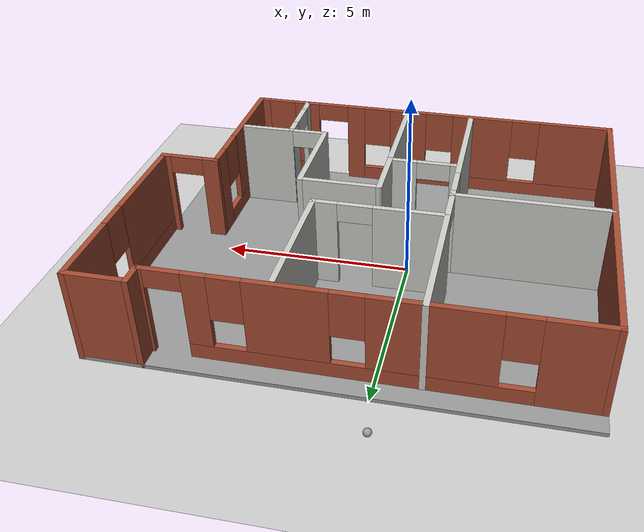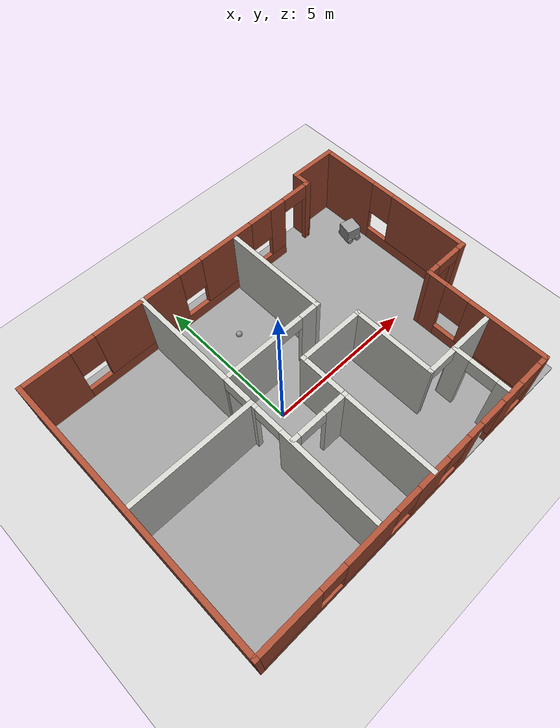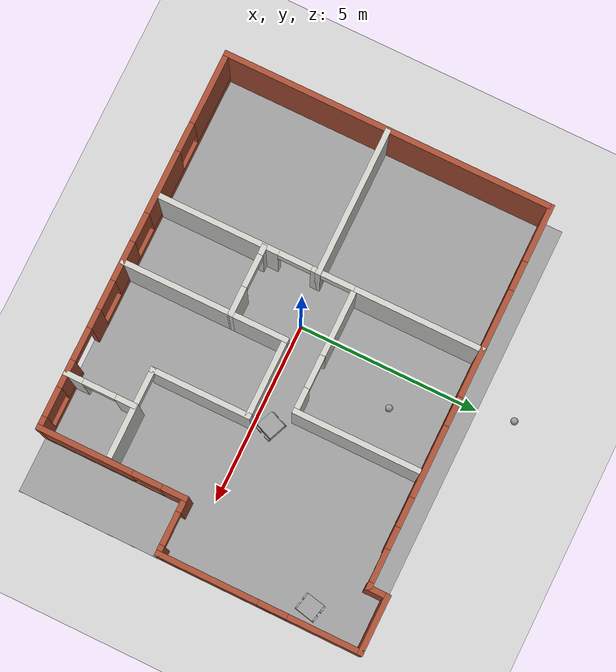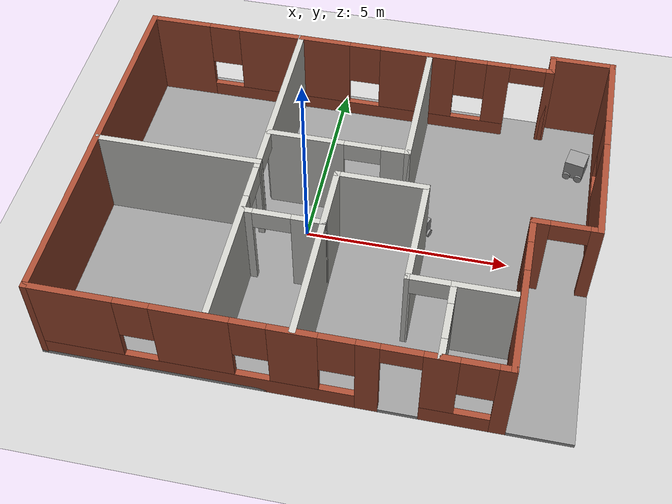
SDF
<sdf version="1.6">
 <world name="default">
  <plugin name="welcome_message" filename="libwelcome_message.so"/>
  <light name="sun" type="directional">
   <pose>0 0 10 0 -0 0</pose>
   <diffuse>0.8 0.8 0.8 1</diffuse>
   <specular>0.2 0.2 0.2 1</specular>
   <attenuation>
    <range>1000</range>
    <constant>0.9</constant>
    <linear>0.01</linear>
    <quadratic>0.001</quadratic>
   </attenuation>
   <direction>-0.5 0.1 -0.9</direction>
  </light>
  <model name="ground_plane">
   <static>1</static>
   <link name="link">
    <collision name="collision">
     <geometry><plane><normal>0 0 1</normal><size>100 100</size></plane></geometry>
     <surface><friction><ode><mu>100</mu><mu2>50</mu2></ode></friction></surface>
    </collision>
    <visual name="visual">
     <cast_shadows>0</cast_shadows>
     <geometry><plane><normal>0 0 1</normal><size>100 100</size></plane></geometry>
     <material>
      <script><uri>file://media/materials/scripts/gazebo.material</uri><name>Gazebo/Grey</name></script>
     </material>
    </visual>
   </link>
  </model>
  <gravity>0 0 -9.8</gravity>
  <magnetic_field>6e-06 2.3e-05 -4.2e-05</magnetic_field>
  <atmosphere type="adiabatic"/>
  <physics name="default_physics" default="0" type="ode">
   <max_step_size>0.001</max_step_size>
   <real_time_factor>1</real_time_factor>
   <real_time_update_rate>1000</real_time_update_rate>
  </physics>
  <scene><ambient>0.4 0.4 0.4 1</ambient><background>0.7 0.7 0.7 1</background><shadows>1</shadows></scene>
  <spherical_coordinates>
   <surface_model>EARTH_WGS84</surface_model>
   <latitude_deg>0</latitude_deg>
   <longitude_deg>0</longitude_deg>
   <elevation>0</elevation>
   <heading_deg>0</heading_deg>
  </spherical_coordinates>
  <model name="Building">
   <pose>0.890532 0.189259 0 0 -0 0</pose>
   <link name="Floor_0">
    <collision name="Floor_0_Collision">
     <geometry><box><size>12.15 9.65 0.1</size></box></geometry>
     <pose>0 0 0.05 0 -0 0</pose>
    </collision>
    <visual name="Floor_0_Visual">
     <pose>0 0 0.05 0 -0 0</pose>
     <geometry><box><size>12.15 9.65 0.1</size></box></geometry>
     <material>
      <script><uri>file://media/materials/scripts/gazebo.material</uri><name>Gazebo/Grey</name></script>
      <ambient>1 1 1 1</ambient>
     </material>
     <meta><layer>0</layer></meta>
    </visual>
   </link>
   <link name="Wall_10">
    <pose>-0.75 4.25 0 0 -0 0</pose>
    <visual name="Wall_10_Visual_0">
     <pose>-4.51925 0 1.25 0 -0 0</pose>
     <geometry><box><size>1.6115 0.15 2.5</size></box></geometry>
     <material>
      <script><uri>file://media/materials/scripts/gazebo.material</uri><name>Gazebo/Bricks</name></script>
      <ambient>1 1 1 1</ambient>
     </material>
     <meta><layer>0</layer></meta>
    </visual>
    <collision name="Wall_10_Collision_0">
     <geometry><box><size>1.6115 0.15 2.5</size></box></geometry>
     <pose>-4.51925 0 1.25 0 -0 0</pose>
    </collision>
    <visual name="Wall_10_Visual_1">
     <pose>5.2153 0 1.25 0 -0 0</pose>
     <geometry><box><size>0.219398 0.15 2.5</size></box></geometry>
     <material>
      <script><uri>file://media/materials/scripts/gazebo.material</uri><name>Gazebo/Bricks</name></script>
      <ambient>1 1 1 1</ambient>
     </material>
     <meta><layer>0</layer></meta>
    </visual>
    <collision name="Wall_10_Collision_1">
     <geometry><box><size>0.219398 0.15 2.5</size></box></geometry>
     <pose>5.2153 0 1.25 0 -0 0</pose>
    </collision>
    <visual name="Wall_10_Visual_2">
     <pose>0.246053 0 0.25 0 -0 0</pose>
     <geometry><box><size>7.9191 0.15 0.5</size></box></geometry>
     <material>
      <script><uri>file://media/materials/scripts/gazebo.material</uri><name>Gazebo/Bricks</name></script>
      <ambient>1 1 1 1</ambient>
     </material>
     <meta><layer>0</layer></meta>
    </visual>
    <collision name="Wall_10_Collision_2">
     <geometry><box><size>7.9191 0.15 0.5</size></box></geometry>
     <pose>0.246053 0 0.25 0 -0 0</pose>
    </collision>
    <visual name="Wall_10_Visual_3">
     <pose>-1.433 0 1.5 0 -0 0</pose>
     <geometry><box><size>2.96099 0.15 2</size></box></geometry>
     <material>
      <script><uri>file://media/materials/scripts/gazebo.material</uri><name>Gazebo/Bricks</name></script>
      <ambient>1 1 1 1</ambient>
     </material>
     <meta><layer>0</layer></meta>
    </visual>
    <collision name="Wall_10_Collision_3">
     <geometry><box><size>2.96099 0.15 2</size></box></geometry>
     <pose>-1.433 0 1.5 0 -0 0</pose>
    </collision>
    <visual name="Wall_10_Visual_4">
     <pose>1.82828 0 1.5 0 -0 0</pose>
     <geometry><box><size>1.96157 0.15 2</size></box></geometry>
     <material>
      <script><uri>file://media/materials/scripts/gazebo.material</uri><name>Gazebo/Bricks</name></script>
      <ambient>1 1 1 1</ambient>
     </material>
     <meta><layer>0</layer></meta>
    </visual>
    <collision name="Wall_10_Collision_4">
     <geometry><box><size>1.96157 0.15 2</size></box></geometry>
     <pose>1.82828 0 1.5 0 -0 0</pose>
    </collision>
    <visual name="Wall_10_Visual_5">
     <pose>3.90733 0 1.5 0 -0 0</pose>
     <geometry><box><size>0.596536 0.15 2</size></box></geometry>
     <material>
      <script><uri>file://media/materials/scripts/gazebo.material</uri><name>Gazebo/Bricks</name></script>
      <ambient>1 1 1 1</ambient>
     </material>
     <meta><layer>0</layer></meta>
    </visual>
    <collision name="Wall_10_Collision_5">
     <geometry><box><size>0.596536 0.15 2</size></box></geometry>
     <pose>3.90733 0 1.5 0 -0 0</pose>
    </collision>
    <visual name="Wall_10_Visual_6">
     <pose>-3.3135 0 1.9 0 -0 0</pose>
     <geometry><box><size>0.8 0.15 1.2</size></box></geometry>
     <material>
      <script><uri>file://media/materials/scripts/gazebo.material</uri><name>Gazebo/Bricks</name></script>
      <ambient>1 1 1 1</ambient>
     </material>
     <meta><layer>0</layer></meta>
    </visual>
    <collision name="Wall_10_Collision_6">
     <geometry><box><size>0.8 0.15 1.2</size></box></geometry>
     <pose>-3.3135 0 1.9 0 -0 0</pose>
    </collision>
    <visual name="Wall_10_Visual_7">
     <pose>0.447498 0 1.9 0 -0 0</pose>
     <geometry><box><size>0.8 0.15 1.2</size></box></geometry>
     <material>
      <script><uri>file://media/materials/scripts/gazebo.material</uri><name>Gazebo/Bricks</name></script>
      <ambient>1 1 1 1</ambient>
     </material>
     <meta><layer>0</layer></meta>
    </visual>
    <collision name="Wall_10_Collision_7">
     <geometry><box><size>0.8 0.15 1.2</size></box></geometry>
     <pose>0.447498 0 1.9 0 -0 0</pose>
    </collision>
    <visual name="Wall_10_Visual_8">
     <pose>3.20907 0 1.9 0 -0 0</pose>
     <geometry><box><size>0.8 0.15 1.2</size></box></geometry>
     <material>
      <script><uri>file://media/materials/scripts/gazebo.material</uri><name>Gazebo/Bricks</name></script>
      <ambient>1 1 1 1</ambient>
     </material>
     <meta><layer>0</layer></meta>
    </visual>
    <collision name="Wall_10_Collision_8">
     <geometry><box><size>0.8 0.15 1.2</size></box></geometry>
     <pose>3.20907 0 1.9 0 -0 0</pose>
    </collision>
    <visual name="Wall_10_Visual_9">
     <pose>4.6556 0 2.25 0 -0 0</pose>
     <geometry><box><size>0.9 0.15 0.5</size></box></geometry>
     <material>
      <script><uri>file://media/materials/scripts/gazebo.material</uri><name>Gazebo/Bricks</name></script>
      <ambient>1 1 1 1</ambient>
     </material>
     <meta><layer>0</layer></meta>
    </visual>
    <collision name="Wall_10_Collision_9">
     <geometry><box><size>0.9 0.15 0.5</size></box></geometry>
     <pose>4.6556 0 2.25 0 -0 0</pose>
    </collision>
   </link>
   <link name="Wall_11">
    <collision name="Wall_11_Collision">
     <geometry><box><size>0.65 0.15 2.5</size></box></geometry>
     <pose>0 0 1.25 0 -0 0</pose>
    </collision>
    <visual name="Wall_11_Visual">
     <pose>0 0 1.25 0 -0 0</pose>
     <geometry><box><size>0.65 0.15 2.5</size></box></geometry>
     <material>
      <script><uri>file://media/materials/scripts/gazebo.material</uri><name>Gazebo/Bricks</name></script>
      <ambient>1 1 1 1</ambient>
     </material>
     <meta><layer>0</layer></meta>
    </visual>
    <pose>4.5 4.5 0 0 -0 1.5708</pose>
   </link>
   <link name="Wall_12">
    <collision name="Wall_12_Collision">
     <geometry><box><size>1.65 0.15 2.5</size></box></geometry>
     <pose>0 0 1.25 0 -0 0</pose>
    </collision>
    <visual name="Wall_12_Visual">
     <pose>0 0 1.25 0 -0 0</pose>
     <geometry><box><size>1.65 0.15 2.5</size></box></geometry>
     <material>
      <script><uri>file://media/materials/scripts/gazebo.material</uri><name>Gazebo/Bricks</name></script>
      <ambient>1 1 1 1</ambient>
     </material>
     <meta><layer>0</layer></meta>
    </visual>
    <pose>5.25 4.75 0 0 -0 0</pose>
   </link>
   <link name="Wall_13">
    <pose>6 2 0 0 0 -1.5708</pose>
    <visual name="Wall_13_Visual_0">
     <pose>-1.79372 0 1.25 0 -0 0</pose>
     <geometry><box><size>2.06257 0.15 2.5</size></box></geometry>
     <material>
      <script><uri>file://media/materials/scripts/gazebo.material</uri><name>Gazebo/Bricks</name></script>
      <ambient>1 1 1 1</ambient>
     </material>
     <meta><layer>0</layer></meta>
    </visual>
    <collision name="Wall_13_Collision_0">
     <geometry><box><size>2.06257 0.15 2.5</size></box></geometry>
     <pose>-1.79372 0 1.25 0 -0 0</pose>
    </collision>
    <visual name="Wall_13_Visual_1">
     <pose>1.03128 0 0.25 0 -0 0</pose>
     <geometry><box><size>3.58743 0.15 0.5</size></box></geometry>
     <material>
      <script><uri>file://media/materials/scripts/gazebo.material</uri><name>Gazebo/Bricks</name></script>
      <ambient>1 1 1 1</ambient>
     </material>
     <meta><layer>0</layer></meta>
    </visual>
    <collision name="Wall_13_Collision_1">
     <geometry><box><size>3.58743 0.15 0.5</size></box></geometry>
     <pose>1.03128 0 0.25 0 -0 0</pose>
    </collision>
    <visual name="Wall_13_Visual_2">
     <pose>1.43128 0 1.5 0 -0 0</pose>
     <geometry><box><size>2.78743 0.15 2</size></box></geometry>
     <material>
      <script><uri>file://media/materials/scripts/gazebo.material</uri><name>Gazebo/Bricks</name></script>
      <ambient>1 1 1 1</ambient>
     </material>
     <meta><layer>0</layer></meta>
    </visual>
    <collision name="Wall_13_Collision_2">
     <geometry><box><size>2.78743 0.15 2</size></box></geometry>
     <pose>1.43128 0 1.5 0 -0 0</pose>
    </collision>
    <visual name="Wall_13_Visual_3">
     <pose>-0.362433 0 1.9 0 -0 0</pose>
     <geometry><box><size>0.8 0.15 1.2</size></box></geometry>
     <material>
      <script><uri>file://media/materials/scripts/gazebo.material</uri><name>Gazebo/Bricks</name></script>
      <ambient>1 1 1 1</ambient>
     </material>
     <meta><layer>0</layer></meta>
    </visual>
    <collision name="Wall_13_Collision_3">
     <geometry><box><size>0.8 0.15 1.2</size></box></geometry>
     <pose>-0.362433 0 1.9 0 -0 0</pose>
    </collision>
   </link>
   <link name="Wall_14">
    <pose>5.25 -0.75 0 0 -0 3.14159</pose>
    <visual name="Wall_14_Visual_0">
     <pose>-0.675418 0 1.25 0 -0 0</pose>
     <geometry><box><size>0.299163 0.15 2.5</size></box></geometry>
     <material>
      <script><uri>file://media/materials/scripts/gazebo.material</uri><name>Gazebo/Bricks</name></script>
      <ambient>1 1 1 1</ambient>
     </material>
     <meta><layer>0</layer></meta>
    </visual>
    <collision name="Wall_14_Collision_0">
     <geometry><box><size>0.299163 0.15 2.5</size></box></geometry>
     <pose>-0.675418 0 1.25 0 -0 0</pose>
    </collision>
    <visual name="Wall_14_Visual_1">
     <pose>0.599582 0 1.25 0 -0 0</pose>
     <geometry><box><size>0.450837 0.15 2.5</size></box></geometry>
     <material>
      <script><uri>file://media/materials/scripts/gazebo.material</uri><name>Gazebo/Bricks</name></script>
      <ambient>1 1 1 1</ambient>
     </material>
     <meta><layer>0</layer></meta>
    </visual>
    <collision name="Wall_14_Collision_1">
     <geometry><box><size>0.450837 0.15 2.5</size></box></geometry>
     <pose>0.599582 0 1.25 0 -0 0</pose>
    </collision>
    <visual name="Wall_14_Visual_2">
     <pose>-0.075837 0 2.25 0 -0 0</pose>
     <geometry><box><size>0.9 0.15 0.5</size></box></geometry>
     <material>
      <script><uri>file://media/materials/scripts/gazebo.material</uri><name>Gazebo/Bricks</name></script>
      <ambient>1 1 1 1</ambient>
     </material>
     <meta><layer>0</layer></meta>
    </visual>
    <collision name="Wall_14_Collision_2">
     <geometry><box><size>0.9 0.15 0.5</size></box></geometry>
     <pose>-0.075837 0 2.25 0 -0 0</pose>
    </collision>
   </link>
   <link name="Wall_15">
    <pose>4.5 -2.75 0 0 0 -1.5708</pose>
    <visual name="Wall_15_Visual_0">
     <pose>-1.71977 0 1.25 0 -0 0</pose>
     <geometry><box><size>0.71046 0.15 2.5</size></box></geometry>
     <material>
      <script><uri>file://media/materials/scripts/gazebo.material</uri><name>Gazebo/Bricks</name></script>
      <ambient>1 1 1 1</ambient>
     </material>
     <meta><layer>0</layer></meta>
    </visual>
    <collision name="Wall_15_Collision_0">
     <geometry><box><size>0.71046 0.15 2.5</size></box></geometry>
     <pose>-1.71977 0 1.25 0 -0 0</pose>
    </collision>
    <visual name="Wall_15_Visual_1">
     <pose>0.35523 0 0.25 0 -0 0</pose>
     <geometry><box><size>3.43954 0.15 0.5</size></box></geometry>
     <material>
      <script><uri>file://media/materials/scripts/gazebo.material</uri><name>Gazebo/Bricks</name></script>
      <ambient>1 1 1 1</ambient>
     </material>
     <meta><layer>0</layer></meta>
    </visual>
    <collision name="Wall_15_Collision_1">
     <geometry><box><size>3.43954 0.15 0.5</size></box></geometry>
     <pose>0.35523 0 0.25 0 -0 0</pose>
    </collision>
    <visual name="Wall_15_Visual_2">
     <pose>0.75523 0 1.5 0 -0 0</pose>
     <geometry><box><size>2.63954 0.15 2</size></box></geometry>
     <material>
      <script><uri>file://media/materials/scripts/gazebo.material</uri><name>Gazebo/Bricks</name></script>
      <ambient>1 1 1 1</ambient>
     </material>
     <meta><layer>0</layer></meta>
    </visual>
    <collision name="Wall_15_Collision_2">
     <geometry><box><size>2.63954 0.15 2</size></box></geometry>
     <pose>0.75523 0 1.5 0 -0 0</pose>
    </collision>
    <visual name="Wall_15_Visual_3">
     <pose>-0.96454 0 1.9 0 -0 0</pose>
     <geometry><box><size>0.8 0.15 1.2</size></box></geometry>
     <material>
      <script><uri>file://media/materials/scripts/gazebo.material</uri><name>Gazebo/Bricks</name></script>
      <ambient>1 1 1 1</ambient>
     </material>
     <meta><layer>0</layer></meta>
    </visual>
    <collision name="Wall_15_Collision_3">
     <geometry><box><size>0.8 0.15 1.2</size></box></geometry>
     <pose>-0.96454 0 1.9 0 -0 0</pose>
    </collision>
   </link>
   <link name="Wall_16">
    <pose>-0.75 -4.75 0 0 -0 3.14159</pose>
    <visual name="Wall_16_Visual_0">
     <pose>-5.13705 0 1.25 0 -0 0</pose>
     <geometry><box><size>0.375908 0.15 2.5</size></box></geometry>
     <material>
      <script><uri>file://media/materials/scripts/gazebo.material</uri><name>Gazebo/Bricks</name></script>
      <ambient>1 1 1 1</ambient>
     </material>
     <meta><layer>0</layer></meta>
    </visual>
    <collision name="Wall_16_Collision_0">
     <geometry><box><size>0.375908 0.15 2.5</size></box></geometry>
     <pose>-5.13705 0 1.25 0 -0 0</pose>
    </collision>
    <visual name="Wall_16_Visual_1">
     <pose>-2.23615 0 1.25 0 -0 0</pose>
     <geometry><box><size>0.518056 0.15 2.5</size></box></geometry>
     <material>
      <script><uri>file://media/materials/scripts/gazebo.material</uri><name>Gazebo/Bricks</name></script>
      <ambient>1 1 1 1</ambient>
     </material>
     <meta><layer>0</layer></meta>
    </visual>
    <collision name="Wall_16_Collision_1">
     <geometry><box><size>0.518056 0.15 2.5</size></box></geometry>
     <pose>-2.23615 0 1.25 0 -0 0</pose>
    </collision>
    <visual name="Wall_16_Visual_2">
     <pose>-4.17213 0 0.25 0 -0 0</pose>
     <geometry><box><size>1.55392 0.15 0.5</size></box></geometry>
     <material>
      <script><uri>file://media/materials/scripts/gazebo.material</uri><name>Gazebo/Bricks</name></script>
      <ambient>1 1 1 1</ambient>
     </material>
     <meta><layer>0</layer></meta>
    </visual>
    <collision name="Wall_16_Collision_2">
     <geometry><box><size>1.55392 0.15 0.5</size></box></geometry>
     <pose>-4.17213 0 0.25 0 -0 0</pose>
    </collision>
    <visual name="Wall_16_Visual_3">
     <pose>1.67394 0 0.25 0 -0 0</pose>
     <geometry><box><size>7.30212 0.15 0.5</size></box></geometry>
     <material>
      <script><uri>file://media/materials/scripts/gazebo.material</uri><name>Gazebo/Bricks</name></script>
      <ambient>1 1 1 1</ambient>
     </material>
     <meta><layer>0</layer></meta>
    </visual>
    <collision name="Wall_16_Collision_3">
     <geometry><box><size>7.30212 0.15 0.5</size></box></geometry>
     <pose>1.67394 0 0.25 0 -0 0</pose>
    </collision>
    <visual name="Wall_16_Visual_4">
     <pose>-3.77213 0 1.5 0 -0 0</pose>
     <geometry><box><size>0.753917 0.15 2</size></box></geometry>
     <material>
      <script><uri>file://media/materials/scripts/gazebo.material</uri><name>Gazebo/Bricks</name></script>
      <ambient>1 1 1 1</ambient>
     </material>
     <meta><layer>0</layer></meta>
    </visual>
    <collision name="Wall_16_Collision_4">
     <geometry><box><size>0.753917 0.15 2</size></box></geometry>
     <pose>-3.77213 0 1.5 0 -0 0</pose>
    </collision>
    <visual name="Wall_16_Visual_5">
     <pose>-3.77213 0 1.5 0 -0 0</pose>
     <geometry><box><size>0.753917 0.15 2</size></box></geometry>
     <material>
      <script><uri>file://media/materials/scripts/gazebo.material</uri><name>Gazebo/Bricks</name></script>
      <ambient>1 1 1 1</ambient>
     </material>
     <meta><layer>0</layer></meta>
    </visual>
    <collision name="Wall_16_Collision_5">
     <geometry><box><size>0.753917 0.15 2</size></box></geometry>
     <pose>-3.77213 0 1.5 0 -0 0</pose>
    </collision>
    <visual name="Wall_16_Visual_6">
     <pose>-0.630295 0 1.5 0 -0 0</pose>
     <geometry><box><size>1.09365 0.15 2</size></box></geometry>
     <material>
      <script><uri>file://media/materials/scripts/gazebo.material</uri><name>Gazebo/Bricks</name></script>
      <ambient>1 1 1 1</ambient>
     </material>
     <meta><layer>0</layer></meta>
    </visual>
    <collision name="Wall_16_Collision_6">
     <geometry><box><size>1.09365 0.15 2</size></box></geometry>
     <pose>-0.630295 0 1.5 0 -0 0</pose>
    </collision>
    <visual name="Wall_16_Visual_7">
     <pose>1.59211 0 1.5 0 -0 0</pose>
     <geometry><box><size>1.75116 0.15 2</size></box></geometry>
     <material>
      <script><uri>file://media/materials/scripts/gazebo.material</uri><name>Gazebo/Bricks</name></script>
      <ambient>1 1 1 1</ambient>
     </material>
     <meta><layer>0</layer></meta>
    </visual>
    <collision name="Wall_16_Collision_7">
     <geometry><box><size>1.75116 0.15 2</size></box></geometry>
     <pose>1.59211 0 1.5 0 -0 0</pose>
    </collision>
    <visual name="Wall_16_Visual_8">
     <pose>4.29635 0 1.5 0 -0 0</pose>
     <geometry><box><size>2.05731 0.15 2</size></box></geometry>
     <material>
      <script><uri>file://media/materials/scripts/gazebo.material</uri><name>Gazebo/Bricks</name></script>
      <ambient>1 1 1 1</ambient>
     </material>
     <meta><layer>0</layer></meta>
    </visual>
    <collision name="Wall_16_Collision_8">
     <geometry><box><size>2.05731 0.15 2</size></box></geometry>
     <pose>4.29635 0 1.5 0 -0 0</pose>
    </collision>
    <visual name="Wall_16_Visual_9">
     <pose>-4.54909 0 1.9 0 -0 0</pose>
     <geometry><box><size>0.8 0.15 1.2</size></box></geometry>
     <material>
      <script><uri>file://media/materials/scripts/gazebo.material</uri><name>Gazebo/Bricks</name></script>
      <ambient>1 1 1 1</ambient>
     </material>
     <meta><layer>0</layer></meta>
    </visual>
    <collision name="Wall_16_Collision_9">
     <geometry><box><size>0.8 0.15 1.2</size></box></geometry>
     <pose>-4.54909 0 1.9 0 -0 0</pose>
    </collision>
    <visual name="Wall_16_Visual_10">
     <pose>-1.57712 0 1.9 0 -0 0</pose>
     <geometry><box><size>0.8 0.15 1.2</size></box></geometry>
     <material>
      <script><uri>file://media/materials/scripts/gazebo.material</uri><name>Gazebo/Bricks</name></script>
      <ambient>1 1 1 1</ambient>
     </material>
     <meta><layer>0</layer></meta>
    </visual>
    <collision name="Wall_16_Collision_10">
     <geometry><box><size>0.8 0.15 1.2</size></box></geometry>
     <pose>-1.57712 0 1.9 0 -0 0</pose>
    </collision>
    <visual name="Wall_16_Visual_11">
     <pose>0.316528 0 1.9 0 -0 0</pose>
     <geometry><box><size>0.8 0.15 1.2</size></box></geometry>
     <material>
      <script><uri>file://media/materials/scripts/gazebo.material</uri><name>Gazebo/Bricks</name></script>
      <ambient>1 1 1 1</ambient>
     </material>
     <meta><layer>0</layer></meta>
    </visual>
    <collision name="Wall_16_Collision_11">
     <geometry><box><size>0.8 0.15 1.2</size></box></geometry>
     <pose>0.316528 0 1.9 0 -0 0</pose>
    </collision>
    <visual name="Wall_16_Visual_12">
     <pose>2.86769 0 1.9 0 -0 0</pose>
     <geometry><box><size>0.8 0.15 1.2</size></box></geometry>
     <material>
      <script><uri>file://media/materials/scripts/gazebo.material</uri><name>Gazebo/Bricks</name></script>
      <ambient>1 1 1 1</ambient>
     </material>
     <meta><layer>0</layer></meta>
    </visual>
    <collision name="Wall_16_Collision_12">
     <geometry><box><size>0.8 0.15 1.2</size></box></geometry>
     <pose>2.86769 0 1.9 0 -0 0</pose>
    </collision>
    <visual name="Wall_16_Visual_13">
     <pose>-2.94517 0 2.25 0 -0 0</pose>
     <geometry><box><size>0.9 0.15 0.5</size></box></geometry>
     <material>
      <script><uri>file://media/materials/scripts/gazebo.material</uri><name>Gazebo/Bricks</name></script>
      <ambient>1 1 1 1</ambient>
     </material>
     <meta><layer>0</layer></meta>
    </visual>
    <collision name="Wall_16_Collision_13">
     <geometry><box><size>0.9 0.15 0.5</size></box></geometry>
     <pose>-2.94517 0 2.25 0 -0 0</pose>
    </collision>
    <visual name="Wall_16_Visual_14">
     <pose>-2.94517 0 2.25 0 -0 0</pose>
     <geometry><box><size>0.9 0.15 0.5</size></box></geometry>
     <material>
      <script><uri>file://media/materials/scripts/gazebo.material</uri><name>Gazebo/Bricks</name></script>
      <ambient>1 1 1 1</ambient>
     </material>
     <meta><layer>0</layer></meta>
    </visual>
    <collision name="Wall_16_Collision_14">
     <geometry><box><size>0.9 0.15 0.5</size></box></geometry>
     <pose>-2.94517 0 2.25 0 -0 0</pose>
    </collision>
   </link>
   <link name="Wall_17">
    <pose>-2 -0.171 0 0 0 -1.5708</pose>
    <visual name="Wall_17_Visual_0">
     <pose>-2.70284 0 1.25 0 -0 0</pose>
     <geometry><box><size>3.59432 0.15 2.5</size></box></geometry>
     <material>
      <script><uri>file://media/materials/scripts/gazebo.material</uri><name>Gazebo/CeilingTiled</name></script>
      <ambient>1 1 1 1</ambient>
     </material>
     <meta><layer>0</layer></meta>
    </visual>
    <collision name="Wall_17_Collision_0">
     <geometry><box><size>3.59432 0.15 2.5</size></box></geometry>
     <pose>-2.70284 0 1.25 0 -0 0</pose>
    </collision>
    <visual name="Wall_17_Visual_1">
     <pose>0.136083 0 1.25 0 -0 0</pose>
     <geometry><box><size>0.283529 0.15 2.5</size></box></geometry>
     <material>
      <script><uri>file://media/materials/scripts/gazebo.material</uri><name>Gazebo/CeilingTiled</name></script>
      <ambient>1 1 1 1</ambient>
     </material>
     <meta><layer>0</layer></meta>
    </visual>
    <collision name="Wall_17_Collision_1">
     <geometry><box><size>0.283529 0.15 2.5</size></box></geometry>
     <pose>0.136083 0 1.25 0 -0 0</pose>
    </collision>
    <visual name="Wall_17_Visual_2">
     <pose>2.83892 0 1.25 0 -0 0</pose>
     <geometry><box><size>3.32215 0.15 2.5</size></box></geometry>
     <material>
      <script><uri>file://media/materials/scripts/gazebo.material</uri><name>Gazebo/CeilingTiled</name></script>
      <ambient>1 1 1 1</ambient>
     </material>
     <meta><layer>0</layer></meta>
    </visual>
    <collision name="Wall_17_Collision_2">
     <geometry><box><size>3.32215 0.15 2.5</size></box></geometry>
     <pose>2.83892 0 1.25 0 -0 0</pose>
    </collision>
    <visual name="Wall_17_Visual_3">
     <pose>-0.455681 0 2.25 0 -0 0</pose>
     <geometry><box><size>0.9 0.15 0.5</size></box></geometry>
     <material>
      <script><uri>file://media/materials/scripts/gazebo.material</uri><name>Gazebo/CeilingTiled</name></script>
      <ambient>1 1 1 1</ambient>
     </material>
     <meta><layer>0</layer></meta>
    </visual>
    <collision name="Wall_17_Collision_3">
     <geometry><box><size>0.9 0.15 0.5</size></box></geometry>
     <pose>-0.455681 0 2.25 0 -0 0</pose>
    </collision>
    <visual name="Wall_17_Visual_4">
     <pose>0.727848 0 2.25 0 -0 0</pose>
     <geometry><box><size>0.9 0.15 0.5</size></box></geometry>
     <material>
      <script><uri>file://media/materials/scripts/gazebo.material</uri><name>Gazebo/CeilingTiled</name></script>
      <ambient>1 1 1 1</ambient>
     </material>
     <meta><layer>0</layer></meta>
    </visual>
    <collision name="Wall_17_Collision_4">
     <geometry><box><size>0.9 0.15 0.5</size></box></geometry>
     <pose>0.727848 0 2.25 0 -0 0</pose>
    </collision>
   </link>
   <link name="Wall_19">
    <collision name="Wall_19_Collision">
     <geometry><box><size>4.103 0.15 2.5</size></box></geometry>
     <pose>0 0 1.25 0 -0 0</pose>
    </collision>
    <visual name="Wall_19_Visual">
     <pose>0 0 1.25 0 -0 0</pose>
     <geometry><box><size>4.103 0.15 2.5</size></box></geometry>
     <material>
      <script><uri>file://media/materials/scripts/gazebo.material</uri><name>Gazebo/CeilingTiled</name></script>
      <ambient>1 1 1 1</ambient>
     </material>
     <meta><layer>0</layer></meta>
    </visual>
    <pose>-3.9765 -0.25 0 0 -0 3.14159</pose>
   </link>
   <link name="Wall_21">
    <pose>-0.284 0.75 0 0 -0 0</pose>
    <visual name="Wall_21_Visual_0">
     <pose>-0.806794 0 1.25 0 -0 0</pose>
     <geometry><box><size>1.88641 0.15 2.5</size></box></geometry>
     <material>
      <script><uri>file://media/materials/scripts/gazebo.material</uri><name>Gazebo/CeilingTiled</name></script>
      <ambient>1 1 1 1</ambient>
     </material>
     <meta><layer>0</layer></meta>
    </visual>
    <collision name="Wall_21_Collision_0">
     <geometry><box><size>1.88641 0.15 2.5</size></box></geometry>
     <pose>-0.806794 0 1.25 0 -0 0</pose>
    </collision>
    <visual name="Wall_21_Visual_1">
     <pose>1.39321 0 1.25 0 -0 0</pose>
     <geometry><box><size>0.713588 0.15 2.5</size></box></geometry>
     <material>
      <script><uri>file://media/materials/scripts/gazebo.material</uri><name>Gazebo/CeilingTiled</name></script>
      <ambient>1 1 1 1</ambient>
     </material>
     <meta><layer>0</layer></meta>
    </visual>
    <collision name="Wall_21_Collision_1">
     <geometry><box><size>0.713588 0.15 2.5</size></box></geometry>
     <pose>1.39321 0 1.25 0 -0 0</pose>
    </collision>
    <visual name="Wall_21_Visual_2">
     <pose>0.586412 0 2.25 0 -0 0</pose>
     <geometry><box><size>0.9 0.15 0.5</size></box></geometry>
     <material>
      <script><uri>file://media/materials/scripts/gazebo.material</uri><name>Gazebo/CeilingTiled</name></script>
      <ambient>1 1 1 1</ambient>
     </material>
     <meta><layer>0</layer></meta>
    </visual>
    <collision name="Wall_21_Collision_2">
     <geometry><box><size>0.9 0.15 0.5</size></box></geometry>
     <pose>0.586412 0 2.25 0 -0 0</pose>
    </collision>
   </link>
   <link name="Wall_22">
    <collision name="Wall_22_Collision">
     <geometry><box><size>3.493 0.15 2.5</size></box></geometry>
     <pose>0 0 1.25 0 -0 0</pose>
    </collision>
    <visual name="Wall_22_Visual">
     <pose>0 0 1.25 0 -0 0</pose>
     <geometry><box><size>3.493 0.15 2.5</size></box></geometry>
     <material>
      <script><uri>file://media/materials/scripts/gazebo.material</uri><name>Gazebo/CeilingTiled</name></script>
      <ambient>1 1 1 1</ambient>
     </material>
     <meta><layer>0</layer></meta>
    </visual>
    <pose>1.391 2.4215 0 0 -0 1.5708</pose>
   </link>
   <link name="Wall_24">
    <pose>-1.034 -1.75 0 0 -0 0</pose>
    <visual name="Wall_24_Visual_0">
     <pose>-0.858964 0 1.25 0 -0 0</pose>
     <geometry><box><size>0.282073 0.15 2.5</size></box></geometry>
     <material>
      <script><uri>file://media/materials/scripts/gazebo.material</uri><name>Gazebo/CeilingTiled</name></script>
      <ambient>1 1 1 1</ambient>
     </material>
     <meta><layer>0</layer></meta>
    </visual>
    <collision name="Wall_24_Collision_0">
     <geometry><box><size>0.282073 0.15 2.5</size></box></geometry>
     <pose>-0.858964 0 1.25 0 -0 0</pose>
    </collision>
    <visual name="Wall_24_Visual_1">
     <pose>0.591036 0 1.25 0 -0 0</pose>
     <geometry><box><size>0.817927 0.15 2.5</size></box></geometry>
     <material>
      <script><uri>file://media/materials/scripts/gazebo.material</uri><name>Gazebo/CeilingTiled</name></script>
      <ambient>1 1 1 1</ambient>
     </material>
     <meta><layer>0</layer></meta>
    </visual>
    <collision name="Wall_24_Collision_1">
     <geometry><box><size>0.817927 0.15 2.5</size></box></geometry>
     <pose>0.591036 0 1.25 0 -0 0</pose>
    </collision>
    <visual name="Wall_24_Visual_2">
     <pose>-0.267927 0 2.25 0 -0 0</pose>
     <geometry><box><size>0.9 0.15 0.5</size></box></geometry>
     <material>
      <script><uri>file://media/materials/scripts/gazebo.material</uri><name>Gazebo/CeilingTiled</name></script>
      <ambient>1 1 1 1</ambient>
     </material>
     <meta><layer>0</layer></meta>
    </visual>
    <collision name="Wall_24_Collision_2">
     <geometry><box><size>0.9 0.15 0.5</size></box></geometry>
     <pose>-0.267927 0 2.25 0 -0 0</pose>
    </collision>
   </link>
   <link name="Wall_25">
    <collision name="Wall_25_Collision">
     <geometry><box><size>3.12197 0.15 2.5</size></box></geometry>
     <pose>0 0 1.25 0 -0 0</pose>
    </collision>
    <visual name="Wall_25_Visual">
     <pose>0 0 1.25 0 -0 0</pose>
     <geometry><box><size>3.12197 0.15 2.5</size></box></geometry>
     <material>
      <script><uri>file://media/materials/scripts/gazebo.material</uri><name>Gazebo/CeilingTiled</name></script>
      <ambient>1 1 1 1</ambient>
     </material>
     <meta><layer>0</layer></meta>
    </visual>
    <pose>-0.109221 -3.23599 0 0 0 -1.57095</pose>
   </link>
   <link name="Wall_27">
    <collision name="Wall_27_Collision">
     <geometry><box><size>1.65 0.15 2.5</size></box></geometry>
     <pose>0 0 1.25 0 -0 0</pose>
    </collision>
    <visual name="Wall_27_Visual">
     <pose>0 0 1.25 0 -0 0</pose>
     <geometry><box><size>1.65 0.15 2.5</size></box></geometry>
     <material>
      <script><uri>file://media/materials/scripts/gazebo.material</uri><name>Gazebo/CeilingTiled</name></script>
      <ambient>1 1 1 1</ambient>
     </material>
     <meta><layer>0</layer></meta>
    </visual>
    <pose>-0.109 -1 0 0 -0 1.5708</pose>
   </link>
   <link name="Wall_28">
    <collision name="Wall_28_Collision">
     <geometry><box><size>2.259 0.15 2.5</size></box></geometry>
     <pose>0 0 1.25 0 -0 0</pose>
    </collision>
    <visual name="Wall_28_Visual">
     <pose>0 0 1.25 0 -0 0</pose>
     <geometry><box><size>2.259 0.15 2.5</size></box></geometry>
     <material>
      <script><uri>file://media/materials/scripts/gazebo.material</uri><name>Gazebo/CeilingTiled</name></script>
      <ambient>1 1 1 1</ambient>
     </material>
     <meta><layer>0</layer></meta>
    </visual>
    <pose>0.9455 -0.25 0 0 -0 0</pose>
   </link>
   <link name="Wall_29">
    <collision name="Wall_29_Collision">
     <geometry><box><size>2.772 0.15 2.5</size></box></geometry>
     <pose>0 0 1.25 0 -0 0</pose>
    </collision>
    <visual name="Wall_29_Visual">
     <pose>0 0 1.25 0 -0 0</pose>
     <geometry><box><size>2.772 0.15 2.5</size></box></geometry>
     <material>
      <script><uri>file://media/materials/scripts/gazebo.material</uri><name>Gazebo/CeilingTiled</name></script>
      <ambient>1 1 1 1</ambient>
     </material>
     <meta><layer>0</layer></meta>
    </visual>
    <pose>2 -1.561 0 0 0 -1.5708</pose>
   </link>
   <link name="Wall_30">
    <pose>3.17028 -2.87199 0 0 -0 1.2e-05</pose>
    <visual name="Wall_30_Visual_0">
     <pose>-1.1901 0 1.25 0 -0 0</pose>
     <geometry><box><size>0.110365 0.15 2.5</size></box></geometry>
     <material>
      <script><uri>file://media/materials/scripts/gazebo.material</uri><name>Gazebo/CeilingTiled</name></script>
      <ambient>1 1 1 1</ambient>
     </material>
     <meta><layer>0</layer></meta>
    </visual>
    <collision name="Wall_30_Collision_0">
     <geometry><box><size>0.110365 0.15 2.5</size></box></geometry>
     <pose>-1.1901 0 1.25 0 -0 0</pose>
    </collision>
    <visual name="Wall_30_Visual_1">
     <pose>0.505183 0 1.25 0 -0 0</pose>
     <geometry><box><size>1.48019 0.15 2.5</size></box></geometry>
     <material>
      <script><uri>file://media/materials/scripts/gazebo.material</uri><name>Gazebo/CeilingTiled</name></script>
      <ambient>1 1 1 1</ambient>
     </material>
     <meta><layer>0</layer></meta>
    </visual>
    <collision name="Wall_30_Collision_1">
     <geometry><box><size>1.48019 0.15 2.5</size></box></geometry>
     <pose>0.505183 0 1.25 0 -0 0</pose>
    </collision>
    <visual name="Wall_30_Visual_2">
     <pose>-0.684913 0 2.25 0 -0 0</pose>
     <geometry><box><size>0.9 0.15 0.5</size></box></geometry>
     <material>
      <script><uri>file://media/materials/scripts/gazebo.material</uri><name>Gazebo/CeilingTiled</name></script>
      <ambient>1 1 1 1</ambient>
     </material>
     <meta><layer>0</layer></meta>
    </visual>
    <collision name="Wall_30_Collision_2">
     <geometry><box><size>0.9 0.15 0.5</size></box></geometry>
     <pose>-0.684913 0 2.25 0 -0 0</pose>
    </collision>
   </link>
   <link name="Wall_32">
    <pose>3 -3.823 0 0 0 -1.5708</pose>
    <visual name="Wall_32_Visual_0">
     <pose>-0.71424 0 1.25 0 -0 0</pose>
     <geometry><box><size>0.57152 0.15 2.5</size></box></geometry>
     <material>
      <script><uri>file://media/materials/scripts/gazebo.material</uri><name>Gazebo/CeilingTiled</name></script>
      <ambient>1 1 1 1</ambient>
     </material>
     <meta><layer>0</layer></meta>
    </visual>
    <collision name="Wall_32_Collision_0">
     <geometry><box><size>0.57152 0.15 2.5</size></box></geometry>
     <pose>-0.71424 0 1.25 0 -0 0</pose>
    </collision>
    <visual name="Wall_32_Visual_1">
     <pose>0.73576 0 1.25 0 -0 0</pose>
     <geometry><box><size>0.52848 0.15 2.5</size></box></geometry>
     <material>
      <script><uri>file://media/materials/scripts/gazebo.material</uri><name>Gazebo/CeilingTiled</name></script>
      <ambient>1 1 1 1</ambient>
     </material>
     <meta><layer>0</layer></meta>
    </visual>
    <collision name="Wall_32_Collision_1">
     <geometry><box><size>0.52848 0.15 2.5</size></box></geometry>
     <pose>0.73576 0 1.25 0 -0 0</pose>
    </collision>
    <visual name="Wall_32_Visual_2">
     <pose>0.02152 0 2.25 0 -0 0</pose>
     <geometry><box><size>0.9 0.15 0.5</size></box></geometry>
     <material>
      <script><uri>file://media/materials/scripts/gazebo.material</uri><name>Gazebo/CeilingTiled</name></script>
      <ambient>1 1 1 1</ambient>
     </material>
     <meta><layer>0</layer></meta>
    </visual>
    <collision name="Wall_32_Collision_2">
     <geometry><box><size>0.9 0.15 0.5</size></box></geometry>
     <pose>0.02152 0 2.25 0 -0 0</pose>
    </collision>
   </link>
   <link name="Wall_9">
    <collision name="Wall_9_Collision">
     <geometry><box><size>9.15 0.15 2.5</size></box></geometry>
     <pose>0 0 1.25 0 -0 0</pose>
    </collision>
    <visual name="Wall_9_Visual">
     <pose>0 0 1.25 0 -0 0</pose>
     <geometry><box><size>9.15 0.15 2.5</size></box></geometry>
     <material>
      <script><uri>file://media/materials/scripts/gazebo.material</uri><name>Gazebo/Bricks</name></script>
      <ambient>1 1 1 1</ambient>
     </material>
     <meta><layer>0</layer></meta>
    </visual>
    <pose>-6 -0.25 0 0 -0 1.5708</pose>
   </link>
   <static>1</static>
  </model>
  <model name="Model">
   <link name="link_0">
    <pose>0.074923 -0.135492 0.11601 0 0.01074 0</pose>
    <inertial>
     <mass>1</mass>
     <inertia>
      <ixx>0.166667</ixx>
      <ixy>0</ixy>
      <ixz>0</ixz>
      <iyy>0.166667</iyy>
      <iyz>0</iyz>
      <izz>0.166667</izz>
     </inertia>
    </inertial>
    <visual name="visual">
     <geometry><box><size>0.5 0.5 0.5</size></box></geometry>
     <material>
      <lighting>1</lighting>
      <script><uri>file://media/materials/scripts/gazebo.material</uri><name>Gazebo/Grey</name></script>
      <ambient>0.3 0.3 0.3 1</ambient>
      <diffuse>0.7 0.7 0.7 1</diffuse>
      <specular>0.01 0.01 0.01 1</specular>
      <emissive>0 0 0 1</emissive>
      <shader type="vertex"><normal_map>__default__</normal_map></shader>
     </material>
    </visual>
    <collision name="collision">
     <geometry><box><size>0.5 0.5 0.5</size></box></geometry>
     <surface>
      <friction>
       <ode><mu>1</mu><mu2>1</mu2><fdir1>0 0 0</fdir1><slip1>0</slip1><slip2>0</slip2></ode>
       <torsional>
        <coefficient>1</coefficient>
        <patch_radius>0</patch_radius>
        <surface_radius>0</surface_radius>
        <use_patch_radius>1</use_patch_radius>
        <ode><slip>0</slip></ode>
       </torsional>
      </friction>
      <bounce><restitution_coefficient>0</restitution_coefficient><threshold>1e+06</threshold></bounce>
      <contact>
       <collide_without_contact>0</collide_without_contact>
       <collide_without_contact_bitmask>1</collide_without_contact_bitmask>
       <collide_bitmask>1</collide_bitmask>
       <ode>
        <soft_cfm>0</soft_cfm>
        <soft_erp>0.2</soft_erp>
        <kp>1e+13</kp>
        <kd>1</kd>
        <max_vel>0.01</max_vel>
        <min_depth>0</min_depth>
       </ode>
       <bullet>
        <split_impulse>1</split_impulse>
        <split_impulse_penetration_threshold>-0.01</split_impulse_penetration_threshold>
        <soft_cfm>0</soft_cfm>
        <soft_erp>0.2</soft_erp>
        <kp>1e+13</kp>
        <kd>1</kd>
       </bullet>
      </contact>
     </surface>
    </collision>
   </link>
   <link name="link_1">
    <pose>-0.078239 -0.410505 -0.082356 1.5707 -0 0</pose>
    <inertial>
     <mass>1</mass>
     <inertia><ixx>0.145833</ixx><ixy>0</ixy><ixz>0</ixz><iyy>0.145833</iyy><iyz>0</iyz><izz>0.125</izz></inertia>
    </inertial>
    <visual name="visual">
     <geometry><cylinder><radius>0.1</radius><length>0.05</length></cylinder></geometry>
     <material>
      <lighting>1</lighting>
      <script><uri>file://media/materials/scripts/gazebo.material</uri><name>Gazebo/Grey</name></script>
      <ambient>0.3 0.3 0.3 1</ambient>
      <diffuse>0.7 0.7 0.7 1</diffuse>
      <specular>0.01 0.01 0.01 1</specular>
      <emissive>0 0 0 1</emissive>
      <shader type="vertex"><normal_map>__default__</normal_map></shader>
     </material>
    </visual>
    <collision name="collision">
     <geometry><cylinder><radius>0.1</radius><length>0.05</length></cylinder></geometry>
     <surface>
      <friction>
       <ode><mu>1</mu><mu2>1</mu2><fdir1>0 0 0</fdir1><slip1>0</slip1><slip2>0</slip2></ode>
       <torsional>
        <coefficient>1</coefficient>
        <patch_radius>0</patch_radius>
        <surface_radius>0</surface_radius>
        <use_patch_radius>1</use_patch_radius>
        <ode><slip>0</slip></ode>
       </torsional>
      </friction>
      <bounce><restitution_coefficient>0</restitution_coefficient><threshold>1e+06</threshold></bounce>
      <contact>
       <collide_without_contact>0</collide_without_contact>
       <collide_without_contact_bitmask>1</collide_without_contact_bitmask>
       <collide_bitmask>1</collide_bitmask>
       <ode>
        <soft_cfm>0</soft_cfm>
        <soft_erp>0.2</soft_erp>
        <kp>1e+13</kp>
        <kd>1</kd>
        <max_vel>0.01</max_vel>
        <min_depth>0</min_depth>
       </ode>
       <bullet>
        <split_impulse>1</split_impulse>
        <split_impulse_penetration_threshold>-0.01</split_impulse_penetration_threshold>
        <soft_cfm>0</soft_cfm>
        <soft_erp>0.2</soft_erp>
        <kp>1e+13</kp>
        <kd>1</kd>
       </bullet>
      </contact>
     </surface>
    </collision>
   </link>
   <link name="link_1_clone">
    <pose>0.227067 -0.410502 -0.085635 1.5707 -0 0</pose>
    <inertial>
     <mass>1</mass>
     <inertia><ixx>0.145833</ixx><ixy>0</ixy><ixz>0</ixz><iyy>0.145833</iyy><iyz>0</iyz><izz>0.125</izz></inertia>
    </inertial>
    <visual name="visual">
     <geometry><cylinder><radius>0.1</radius><length>0.05</length></cylinder></geometry>
     <material>
      <lighting>1</lighting>
      <script><uri>file://media/materials/scripts/gazebo.material</uri><name>Gazebo/Grey</name></script>
      <ambient>0.3 0.3 0.3 1</ambient>
      <diffuse>0.7 0.7 0.7 1</diffuse>
      <specular>0.01 0.01 0.01 1</specular>
      <emissive>0 0 0 1</emissive>
      <shader type="vertex"><normal_map>__default__</normal_map></shader>
     </material>
    </visual>
    <collision name="collision">
     <geometry><cylinder><radius>0.1</radius><length>0.05</length></cylinder></geometry>
     <surface>
      <friction>
       <ode><mu>1</mu><mu2>1</mu2><fdir1>0 0 0</fdir1><slip1>0</slip1><slip2>0</slip2></ode>
       <torsional>
        <coefficient>1</coefficient>
        <patch_radius>0</patch_radius>
        <surface_radius>0</surface_radius>
        <use_patch_radius>1</use_patch_radius>
        <ode><slip>0</slip></ode>
       </torsional>
      </friction>
      <bounce><restitution_coefficient>0</restitution_coefficient><threshold>1e+06</threshold></bounce>
      <contact>
       <collide_without_contact>0</collide_without_contact>
       <collide_without_contact_bitmask>1</collide_without_contact_bitmask>
       <collide_bitmask>1</collide_bitmask>
       <ode>
        <soft_cfm>0</soft_cfm>
        <soft_erp>0.2</soft_erp>
        <kp>1e+13</kp>
        <kd>1</kd>
        <max_vel>0.01</max_vel>
        <min_depth>0</min_depth>
       </ode>
       <bullet>
        <split_impulse>1</split_impulse>
        <split_impulse_penetration_threshold>-0.01</split_impulse_penetration_threshold>
        <soft_cfm>0</soft_cfm>
        <soft_erp>0.2</soft_erp>
        <kp>1e+13</kp>
        <kd>1</kd>
       </bullet>
      </contact>
     </surface>
    </collision>
   </link>
   <link name="link_1_clone_0">
    <pose>-0.077748 0.139518 -0.082385 1.5707 -0 0</pose>
    <inertial>
     <mass>1</mass>
     <inertia><ixx>0.145833</ixx><ixy>0</ixy><ixz>0</ixz><iyy>0.145833</iyy><iyz>0</iyz><izz>0.125</izz></inertia>
    </inertial>
    <visual name="visual">
     <geometry><cylinder><radius>0.1</radius><length>0.05</length></cylinder></geometry>
     <material>
      <lighting>1</lighting>
      <script><uri>file://media/materials/scripts/gazebo.material</uri><name>Gazebo/Grey</name></script>
      <ambient>0.3 0.3 0.3 1</ambient>
      <diffuse>0.7 0.7 0.7 1</diffuse>
      <specular>0.01 0.01 0.01 1</specular>
      <emissive>0 0 0 1</emissive>
      <shader type="vertex"><normal_map>__default__</normal_map></shader>
     </material>
    </visual>
    <collision name="collision">
     <geometry><cylinder><radius>0.1</radius><length>0.05</length></cylinder></geometry>
     <surface>
      <friction>
       <ode><mu>1</mu><mu2>1</mu2><fdir1>0 0 0</fdir1><slip1>0</slip1><slip2>0</slip2></ode>
       <torsional>
        <coefficient>1</coefficient>
        <patch_radius>0</patch_radius>
        <surface_radius>0</surface_radius>
        <use_patch_radius>1</use_patch_radius>
        <ode><slip>0</slip></ode>
       </torsional>
      </friction>
      <bounce><restitution_coefficient>0</restitution_coefficient><threshold>1e+06</threshold></bounce>
      <contact>
       <collide_without_contact>0</collide_without_contact>
       <collide_without_contact_bitmask>1</collide_without_contact_bitmask>
       <collide_bitmask>1</collide_bitmask>
       <ode>
        <soft_cfm>0</soft_cfm>
        <soft_erp>0.2</soft_erp>
        <kp>1e+13</kp>
        <kd>1</kd>
        <max_vel>0.01</max_vel>
        <min_depth>0</min_depth>
       </ode>
       <bullet>
        <split_impulse>1</split_impulse>
        <split_impulse_penetration_threshold>-0.01</split_impulse_penetration_threshold>
        <soft_cfm>0</soft_cfm>
        <soft_erp>0.2</soft_erp>
        <kp>1e+13</kp>
        <kd>1</kd>
       </bullet>
      </contact>
     </surface>
    </collision>
   </link>
   <link name="link_1_clone_1">
    <pose>0.227067 0.139518 -0.085635 1.5707 -0 0</pose>
    <inertial>
     <mass>1</mass>
     <inertia><ixx>0.145833</ixx><ixy>0</ixy><ixz>0</ixz><iyy>0.145833</iyy><iyz>0</iyz><izz>0.125</izz></inertia>
    </inertial>
    <visual name="visual">
     <geometry><cylinder><radius>0.1</radius><length>0.05</length></cylinder></geometry>
     <material>
      <lighting>1</lighting>
      <script><uri>file://media/materials/scripts/gazebo.material</uri><name>Gazebo/Grey</name></script>
      <ambient>0.3 0.3 0.3 1</ambient>
      <diffuse>0.7 0.7 0.7 1</diffuse>
      <specular>0.01 0.01 0.01 1</specular>
      <emissive>0 0 0 1</emissive>
      <shader type="vertex"><normal_map>__default__</normal_map></shader>
     </material>
    </visual>
    <collision name="collision">
     <geometry><cylinder><radius>0.1</radius><length>0.05</length></cylinder></geometry>
     <surface>
      <friction>
       <ode><mu>1</mu><mu2>1</mu2><fdir1>0 0 0</fdir1><slip1>0</slip1><slip2>0</slip2></ode>
       <torsional>
        <coefficient>1</coefficient>
        <patch_radius>0</patch_radius>
        <surface_radius>0</surface_radius>
        <use_patch_radius>1</use_patch_radius>
        <ode><slip>0</slip></ode>
       </torsional>
      </friction>
      <bounce><restitution_coefficient>0</restitution_coefficient><threshold>1e+06</threshold></bounce>
      <contact>
       <collide_without_contact>0</collide_without_contact>
       <collide_without_contact_bitmask>1</collide_without_contact_bitmask>
       <collide_bitmask>1</collide_bitmask>
       <ode>
        <soft_cfm>0</soft_cfm>
        <soft_erp>0.2</soft_erp>
        <kp>1e+13</kp>
        <kd>1</kd>
        <max_vel>0.01</max_vel>
        <min_depth>0</min_depth>
       </ode>
       <bullet>
        <split_impulse>1</split_impulse>
        <split_impulse_penetration_threshold>-0.01</split_impulse_penetration_threshold>
        <soft_cfm>0</soft_cfm>
        <soft_erp>0.2</soft_erp>
        <kp>1e+13</kp>
        <kd>1</kd>
       </bullet>
      </contact>
     </surface>
    </collision>
   </link>
   <joint name="link_0_JOINT_5" type="revolute">
    <parent>link_0</parent>
    <child>link_1</child>
    <axis>
     <xyz>0 0 1</xyz>
     <use_parent_model_frame>0</use_parent_model_frame>
     <limit>
      <lower>-1.79769e+308</lower>
      <upper>1.79769e+308</upper>
      <effort>-1</effort>
      <velocity>-1</velocity>
     </limit>
     <dynamics>
      <spring_reference>0</spring_reference>
      <spring_stiffness>0</spring_stiffness>
      <damping>0</damping>
     </dynamics>
    </axis>
    <physics>
     <ode><limit><cfm>0</cfm><erp>0.2</erp></limit><suspension><cfm>0</cfm><erp>0.2</erp></suspension></ode>
    </physics>
   </joint>
   <joint name="link_0_JOINT_6" type="revolute">
    <parent>link_0</parent>
    <child>link_1_clone</child>
    <axis>
     <xyz>0 0 1</xyz>
     <use_parent_model_frame>0</use_parent_model_frame>
     <limit>
      <lower>-1.79769e+308</lower>
      <upper>1.79769e+308</upper>
      <effort>-1</effort>
      <velocity>-1</velocity>
     </limit>
     <dynamics>
      <spring_reference>0</spring_reference>
      <spring_stiffness>0</spring_stiffness>
      <damping>0</damping>
     </dynamics>
    </axis>
    <physics>
     <ode><limit><cfm>0</cfm><erp>0.2</erp></limit><suspension><cfm>0</cfm><erp>0.2</erp></suspension></ode>
    </physics>
   </joint>
   <joint name="link_0_JOINT_7" type="revolute">
    <parent>link_0</parent>
    <child>link_1_clone_0</child>
    <axis>
     <xyz>0 0 1</xyz>
     <use_parent_model_frame>0</use_parent_model_frame>
     <limit>
      <lower>-1.79769e+308</lower>
      <upper>1.79769e+308</upper>
      <effort>-1</effort>
      <velocity>-1</velocity>
     </limit>
     <dynamics>
      <spring_reference>0</spring_reference>
      <spring_stiffness>0</spring_stiffness>
      <damping>0</damping>
      <friction>0</friction>
     </dynamics>
    </axis>
    <physics>
     <ode><limit><cfm>0</cfm><erp>0.2</erp></limit><suspension><cfm>0</cfm><erp>0.2</erp></suspension></ode>
    </physics>
   </joint>
   <joint name="link_0_JOINT_8" type="revolute">
    <parent>link_0</parent>
    <child>link_1_clone_1</child>
    <axis>
     <xyz>0 0 1</xyz>
     <use_parent_model_frame>0</use_parent_model_frame>
     <limit>
      <lower>-1.79769e+308</lower>
      <upper>1.79769e+308</upper>
      <effort>-1</effort>
      <velocity>-1</velocity>
     </limit>
     <dynamics>
      <spring_reference>0</spring_reference>
      <spring_stiffness>0</spring_stiffness>
      <damping>0</damping>
     </dynamics>
    </axis>
    <physics>
     <ode><limit><cfm>0</cfm><erp>0.2</erp></limit><suspension><cfm>0</cfm><erp>0.2</erp></suspension></ode>
    </physics>
   </joint>
   <static>0</static>
   <pose>2.52845 0.428304 0.283209 4.3e-05 -0.010726 1.1795</pose>
  </model>
  <model name="Model_0">
   <link name="link_0">
    <pose>0.074923 -0.135492 0.11601 0 0.01074 0</pose>
    <inertial>
     <mass>1</mass>
     <inertia>
      <ixx>0.166667</ixx>
      <ixy>0</ixy>
      <ixz>0</ixz>
      <iyy>0.166667</iyy>
      <iyz>0</iyz>
      <izz>0.166667</izz>
     </inertia>
    </inertial>
    <visual name="visual">
     <geometry><box><size>0.5 0.5 0.5</size></box></geometry>
     <material>
      <lighting>1</lighting>
      <script><uri>file://media/materials/scripts/gazebo.material</uri><name>Gazebo/Grey</name></script>
      <ambient>0.3 0.3 0.3 1</ambient>
      <diffuse>0.7 0.7 0.7 1</diffuse>
      <specular>0.01 0.01 0.01 1</specular>
      <emissive>0 0 0 1</emissive>
      <shader type="vertex"><normal_map>__default__</normal_map></shader>
     </material>
    </visual>
    <collision name="collision">
     <geometry><box><size>0.5 0.5 0.5</size></box></geometry>
     <surface>
      <friction>
       <ode><mu>1</mu><mu2>1</mu2><fdir1>0 0 0</fdir1><slip1>0</slip1><slip2>0</slip2></ode>
       <torsional>
        <coefficient>1</coefficient>
        <patch_radius>0</patch_radius>
        <surface_radius>0</surface_radius>
        <use_patch_radius>1</use_patch_radius>
        <ode><slip>0</slip></ode>
       </torsional>
      </friction>
      <bounce><restitution_coefficient>0</restitution_coefficient><threshold>1e+06</threshold></bounce>
      <contact>
       <collide_without_contact>0</collide_without_contact>
       <collide_without_contact_bitmask>1</collide_without_contact_bitmask>
       <collide_bitmask>1</collide_bitmask>
       <ode>
        <soft_cfm>0</soft_cfm>
        <soft_erp>0.2</soft_erp>
        <kp>1e+13</kp>
        <kd>1</kd>
        <max_vel>0.01</max_vel>
        <min_depth>0</min_depth>
       </ode>
       <bullet>
        <split_impulse>1</split_impulse>
        <split_impulse_penetration_threshold>-0.01</split_impulse_penetration_threshold>
        <soft_cfm>0</soft_cfm>
        <soft_erp>0.2</soft_erp>
        <kp>1e+13</kp>
        <kd>1</kd>
       </bullet>
      </contact>
     </surface>
    </collision>
   </link>
   <link name="link_1">
    <pose>-0.078239 -0.410505 -0.082356 1.5707 -0 0</pose>
    <inertial>
     <mass>1</mass>
     <inertia><ixx>0.145833</ixx><ixy>0</ixy><ixz>0</ixz><iyy>0.145833</iyy><iyz>0</iyz><izz>0.125</izz></inertia>
    </inertial>
    <visual name="visual">
     <geometry><cylinder><radius>0.1</radius><length>0.05</length></cylinder></geometry>
     <material>
      <lighting>1</lighting>
      <script><uri>file://media/materials/scripts/gazebo.material</uri><name>Gazebo/Grey</name></script>
      <ambient>0.3 0.3 0.3 1</ambient>
      <diffuse>0.7 0.7 0.7 1</diffuse>
      <specular>0.01 0.01 0.01 1</specular>
      <emissive>0 0 0 1</emissive>
      <shader type="vertex"><normal_map>__default__</normal_map></shader>
     </material>
    </visual>
    <collision name="collision">
     <geometry><cylinder><radius>0.1</radius><length>0.05</length></cylinder></geometry>
     <surface>
      <friction>
       <ode><mu>1</mu><mu2>1</mu2><fdir1>0 0 0</fdir1><slip1>0</slip1><slip2>0</slip2></ode>
       <torsional>
        <coefficient>1</coefficient>
        <patch_radius>0</patch_radius>
        <surface_radius>0</surface_radius>
        <use_patch_radius>1</use_patch_radius>
        <ode><slip>0</slip></ode>
       </torsional>
      </friction>
      <bounce><restitution_coefficient>0</restitution_coefficient><threshold>1e+06</threshold></bounce>
      <contact>
       <collide_without_contact>0</collide_without_contact>
       <collide_without_contact_bitmask>1</collide_without_contact_bitmask>
       <collide_bitmask>1</collide_bitmask>
       <ode>
        <soft_cfm>0</soft_cfm>
        <soft_erp>0.2</soft_erp>
        <kp>1e+13</kp>
        <kd>1</kd>
        <max_vel>0.01</max_vel>
        <min_depth>0</min_depth>
       </ode>
       <bullet>
        <split_impulse>1</split_impulse>
        <split_impulse_penetration_threshold>-0.01</split_impulse_penetration_threshold>
        <soft_cfm>0</soft_cfm>
        <soft_erp>0.2</soft_erp>
        <kp>1e+13</kp>
        <kd>1</kd>
       </bullet>
      </contact>
     </surface>
    </collision>
   </link>
   <link name="link_1_clone">
    <pose>0.227067 -0.410502 -0.085635 1.5707 -0 0</pose>
    <inertial>
     <mass>1</mass>
     <inertia><ixx>0.145833</ixx><ixy>0</ixy><ixz>0</ixz><iyy>0.145833</iyy><iyz>0</iyz><izz>0.125</izz></inertia>
    </inertial>
    <visual name="visual">
     <geometry><cylinder><radius>0.1</radius><length>0.05</length></cylinder></geometry>
     <material>
      <lighting>1</lighting>
      <script><uri>file://media/materials/scripts/gazebo.material</uri><name>Gazebo/Grey</name></script>
      <ambient>0.3 0.3 0.3 1</ambient>
      <diffuse>0.7 0.7 0.7 1</diffuse>
      <specular>0.01 0.01 0.01 1</specular>
      <emissive>0 0 0 1</emissive>
      <shader type="vertex"><normal_map>__default__</normal_map></shader>
     </material>
    </visual>
    <collision name="collision">
     <geometry><cylinder><radius>0.1</radius><length>0.05</length></cylinder></geometry>
     <surface>
      <friction>
       <ode><mu>1</mu><mu2>1</mu2><fdir1>0 0 0</fdir1><slip1>0</slip1><slip2>0</slip2></ode>
       <torsional>
        <coefficient>1</coefficient>
        <patch_radius>0</patch_radius>
        <surface_radius>0</surface_radius>
        <use_patch_radius>1</use_patch_radius>
        <ode><slip>0</slip></ode>
       </torsional>
      </friction>
      <bounce><restitution_coefficient>0</restitution_coefficient><threshold>1e+06</threshold></bounce>
      <contact>
       <collide_without_contact>0</collide_without_contact>
       <collide_without_contact_bitmask>1</collide_without_contact_bitmask>
       <collide_bitmask>1</collide_bitmask>
       <ode>
        <soft_cfm>0</soft_cfm>
        <soft_erp>0.2</soft_erp>
        <kp>1e+13</kp>
        <kd>1</kd>
        <max_vel>0.01</max_vel>
        <min_depth>0</min_depth>
       </ode>
       <bullet>
        <split_impulse>1</split_impulse>
        <split_impulse_penetration_threshold>-0.01</split_impulse_penetration_threshold>
        <soft_cfm>0</soft_cfm>
        <soft_erp>0.2</soft_erp>
        <kp>1e+13</kp>
        <kd>1</kd>
       </bullet>
      </contact>
     </surface>
    </collision>
   </link>
   <link name="link_1_clone_0">
    <pose>-0.077748 0.139518 -0.082385 1.5707 -0 0</pose>
    <inertial>
     <mass>1</mass>
     <inertia><ixx>0.145833</ixx><ixy>0</ixy><ixz>0</ixz><iyy>0.145833</iyy><iyz>0</iyz><izz>0.125</izz></inertia>
    </inertial>
    <visual name="visual">
     <geometry><cylinder><radius>0.1</radius><length>0.05</length></cylinder></geometry>
     <material>
      <lighting>1</lighting>
      <script><uri>file://media/materials/scripts/gazebo.material</uri><name>Gazebo/Grey</name></script>
      <ambient>0.3 0.3 0.3 1</ambient>
      <diffuse>0.7 0.7 0.7 1</diffuse>
      <specular>0.01 0.01 0.01 1</specular>
      <emissive>0 0 0 1</emissive>
      <shader type="vertex"><normal_map>__default__</normal_map></shader>
     </material>
    </visual>
    <collision name="collision">
     <geometry><cylinder><radius>0.1</radius><length>0.05</length></cylinder></geometry>
     <surface>
      <friction>
       <ode><mu>1</mu><mu2>1</mu2><fdir1>0 0 0</fdir1><slip1>0</slip1><slip2>0</slip2></ode>
       <torsional>
        <coefficient>1</coefficient>
        <patch_radius>0</patch_radius>
        <surface_radius>0</surface_radius>
        <use_patch_radius>1</use_patch_radius>
        <ode><slip>0</slip></ode>
       </torsional>
      </friction>
      <bounce><restitution_coefficient>0</restitution_coefficient><threshold>1e+06</threshold></bounce>
      <contact>
       <collide_without_contact>0</collide_without_contact>
       <collide_without_contact_bitmask>1</collide_without_contact_bitmask>
       <collide_bitmask>1</collide_bitmask>
       <ode>
        <soft_cfm>0</soft_cfm>
        <soft_erp>0.2</soft_erp>
        <kp>1e+13</kp>
        <kd>1</kd>
        <max_vel>0.01</max_vel>
        <min_depth>0</min_depth>
       </ode>
       <bullet>
        <split_impulse>1</split_impulse>
        <split_impulse_penetration_threshold>-0.01</split_impulse_penetration_threshold>
        <soft_cfm>0</soft_cfm>
        <soft_erp>0.2</soft_erp>
        <kp>1e+13</kp>
        <kd>1</kd>
       </bullet>
      </contact>
     </surface>
    </collision>
   </link>
   <link name="link_1_clone_1">
    <pose>0.227067 0.139518 -0.085635 1.5707 -0 0</pose>
    <inertial>
     <mass>1</mass>
     <inertia><ixx>0.145833</ixx><ixy>0</ixy><ixz>0</ixz><iyy>0.145833</iyy><iyz>0</iyz><izz>0.125</izz></inertia>
    </inertial>
    <visual name="visual">
     <geometry><cylinder><radius>0.1</radius><length>0.05</length></cylinder></geometry>
     <material>
      <lighting>1</lighting>
      <script><uri>file://media/materials/scripts/gazebo.material</uri><name>Gazebo/Grey</name></script>
      <ambient>0.3 0.3 0.3 1</ambient>
      <diffuse>0.7 0.7 0.7 1</diffuse>
      <specular>0.01 0.01 0.01 1</specular>
      <emissive>0 0 0 1</emissive>
      <shader type="vertex"><normal_map>__default__</normal_map></shader>
     </material>
    </visual>
    <collision name="collision">
     <geometry><cylinder><radius>0.1</radius><length>0.05</length></cylinder></geometry>
     <surface>
      <friction>
       <ode><mu>1</mu><mu2>1</mu2><fdir1>0 0 0</fdir1><slip1>0</slip1><slip2>0</slip2></ode>
       <torsional>
        <coefficient>1</coefficient>
        <patch_radius>0</patch_radius>
        <surface_radius>0</surface_radius>
        <use_patch_radius>1</use_patch_radius>
        <ode><slip>0</slip></ode>
       </torsional>
      </friction>
      <bounce><restitution_coefficient>0</restitution_coefficient><threshold>1e+06</threshold></bounce>
      <contact>
       <collide_without_contact>0</collide_without_contact>
       <collide_without_contact_bitmask>1</collide_without_contact_bitmask>
       <collide_bitmask>1</collide_bitmask>
       <ode>
        <soft_cfm>0</soft_cfm>
        <soft_erp>0.2</soft_erp>
        <kp>1e+13</kp>
        <kd>1</kd>
        <max_vel>0.01</max_vel>
        <min_depth>0</min_depth>
       </ode>
       <bullet>
        <split_impulse>1</split_impulse>
        <split_impulse_penetration_threshold>-0.01</split_impulse_penetration_threshold>
        <soft_cfm>0</soft_cfm>
        <soft_erp>0.2</soft_erp>
        <kp>1e+13</kp>
        <kd>1</kd>
       </bullet>
      </contact>
     </surface>
    </collision>
   </link>
   <joint name="link_0_JOINT_5" type="revolute">
    <parent>link_0</parent>
    <child>link_1</child>
    <axis>
     <xyz>0 0 1</xyz>
     <use_parent_model_frame>0</use_parent_model_frame>
     <limit>
      <lower>-1.79769e+308</lower>
      <upper>1.79769e+308</upper>
      <effort>-1</effort>
      <velocity>-1</velocity>
     </limit>
     <dynamics>
      <spring_reference>0</spring_reference>
      <spring_stiffness>0</spring_stiffness>
      <damping>0</damping>
     </dynamics>
    </axis>
    <physics>
     <ode><limit><cfm>0</cfm><erp>0.2</erp></limit><suspension><cfm>0</cfm><erp>0.2</erp></suspension></ode>
    </physics>
   </joint>
   <joint name="link_0_JOINT_6" type="revolute">
    <parent>link_0</parent>
    <child>link_1_clone</child>
    <axis>
     <xyz>0 0 1</xyz>
     <use_parent_model_frame>0</use_parent_model_frame>
     <limit>
      <lower>-1.79769e+308</lower>
      <upper>1.79769e+308</upper>
      <effort>-1</effort>
      <velocity>-1</velocity>
     </limit>
     <dynamics>
      <spring_reference>0</spring_reference>
      <spring_stiffness>0</spring_stiffness>
      <damping>0</damping>
     </dynamics>
    </axis>
    <physics>
     <ode><limit><cfm>0</cfm><erp>0.2</erp></limit><suspension><cfm>0</cfm><erp>0.2</erp></suspension></ode>
    </physics>
   </joint>
   <joint name="link_0_JOINT_7" type="revolute">
    <parent>link_0</parent>
    <child>link_1_clone_0</child>
    <axis>
     <xyz>0 0 1</xyz>
     <use_parent_model_frame>0</use_parent_model_frame>
     <limit>
      <lower>-1.79769e+308</lower>
      <upper>1.79769e+308</upper>
      <effort>-1</effort>
      <velocity>-1</velocity>
     </limit>
     <dynamics>
      <spring_reference>0</spring_reference>
      <spring_stiffness>0</spring_stiffness>
      <damping>0</damping>
      <friction>0</friction>
     </dynamics>
    </axis>
    <physics>
     <ode><limit><cfm>0</cfm><erp>0.2</erp></limit><suspension><cfm>0</cfm><erp>0.2</erp></suspension></ode>
    </physics>
   </joint>
   <joint name="link_0_JOINT_8" type="revolute">
    <parent>link_0</parent>
    <child>link_1_clone_1</child>
    <axis>
     <xyz>0 0 1</xyz>
     <use_parent_model_frame>0</use_parent_model_frame>
     <limit>
      <lower>-1.79769e+308</lower>
      <upper>1.79769e+308</upper>
      <effort>-1</effort>
      <velocity>-1</velocity>
     </limit>
     <dynamics>
      <spring_reference>0</spring_reference>
      <spring_stiffness>0</spring_stiffness>
      <damping>0</damping>
     </dynamics>
    </axis>
    <physics>
     <ode><limit><cfm>0</cfm><erp>0.2</erp></limit><suspension><cfm>0</cfm><erp>0.2</erp></suspension></ode>
    </physics>
   </joint>
   <static>0</static>
   <pose>6.35212 3.4959 0.283207 3.4e-05 -0.010739 -0.218597</pose>
  </model>
  <model name="my_ball">
   <link name="link_0">
    <pose>1e-06 0 0 0 -0 0</pose>
    <inertial>
     <mass>1</mass>
     <inertia><ixx>0.1</ixx><ixy>0</ixy><ixz>0</ixz><iyy>0.1</iyy><iyz>0</iyz><izz>0.1</izz></inertia>
    </inertial>
    <visual name="visual">
     <geometry><sphere><radius>0.1</radius></sphere></geometry>
     <material>
      <lighting>1</lighting>
      <script><uri>file://media/materials/scripts/gazebo.material</uri><name>Gazebo/Grey</name></script>
      <ambient>1 1 1 1</ambient>
      <diffuse>1 1 1 1</diffuse>
      <specular>1 1 1 1</specular>
      <emissive>1 1 1 1</emissive>
      <shader type="vertex"><normal_map>__default__</normal_map></shader>
     </material>
    </visual>
    <collision name="collision">
     <geometry><sphere><radius>0.1</radius></sphere></geometry>
     <surface>
      <friction>
       <ode><mu>1</mu><mu2>1</mu2><fdir1>0 0 0</fdir1><slip1>0</slip1><slip2>0</slip2></ode>
       <torsional>
        <coefficient>1</coefficient>
        <patch_radius>0</patch_radius>
        <surface_radius>0</surface_radius>
        <use_patch_radius>1</use_patch_radius>
        <ode><slip>0</slip></ode>
       </torsional>
      </friction>
      <bounce><restitution_coefficient>0</restitution_coefficient><threshold>1e+06</threshold></bounce>
      <contact>
       <collide_without_contact>0</collide_without_contact>
       <collide_without_contact_bitmask>1</collide_without_contact_bitmask>
       <collide_bitmask>1</collide_bitmask>
       <ode>
        <soft_cfm>0</soft_cfm>
        <soft_erp>0.2</soft_erp>
        <kp>1e+13</kp>
        <kd>1</kd>
        <max_vel>0.01</max_vel>
        <min_depth>0</min_depth>
       </ode>
       <bullet>
        <split_impulse>1</split_impulse>
        <split_impulse_penetration_threshold>-0.01</split_impulse_penetration_threshold>
        <soft_cfm>0</soft_cfm>
        <soft_erp>0.2</soft_erp>
        <kp>1e+13</kp>
        <kd>1</kd>
       </bullet>
      </contact>
     </surface>
    </collision>
   </link>
   <static>0</static>
   <pose>0.934381 2.95465 0.2 0 -0 0</pose>
  </model>
  <model name="my_ball_0">
   <link name="link_0">
    <pose>1e-06 0 0 0 -0 0</pose>
    <inertial>
     <mass>1</mass>
     <inertia><ixx>0.1</ixx><ixy>0</ixy><ixz>0</ixz><iyy>0.1</iyy><iyz>0</iyz><izz>0.1</izz></inertia>
    </inertial>
    <visual name="visual">
     <geometry><sphere><radius>0.1</radius></sphere></geometry>
     <material>
      <lighting>1</lighting>
      <script><uri>file://media/materials/scripts/gazebo.material</uri><name>Gazebo/Grey</name></script>
      <ambient>1 1 1 1</ambient>
      <diffuse>1 1 1 1</diffuse>
      <specular>1 1 1 1</specular>
      <emissive>1 1 1 1</emissive>
      <shader type="vertex"><normal_map>__default__</normal_map></shader>
     </material>
    </visual>
    <collision name="collision">
     <geometry><sphere><radius>0.1</radius></sphere></geometry>
     <surface>
      <friction>
       <ode><mu>1</mu><mu2>1</mu2><fdir1>0 0 0</fdir1><slip1>0</slip1><slip2>0</slip2></ode>
       <torsional>
        <coefficient>1</coefficient>
        <patch_radius>0</patch_radius>
        <surface_radius>0</surface_radius>
        <use_patch_radius>1</use_patch_radius>
        <ode><slip>0</slip></ode>
       </torsional>
      </friction>
      <bounce><restitution_coefficient>0</restitution_coefficient><threshold>1e+06</threshold></bounce>
      <contact>
       <collide_without_contact>0</collide_without_contact>
       <collide_without_contact_bitmask>1</collide_without_contact_bitmask>
       <collide_bitmask>1</collide_bitmask>
       <ode>
        <soft_cfm>0</soft_cfm>
        <soft_erp>0.2</soft_erp>
        <kp>1e+13</kp>
        <kd>1</kd>
        <max_vel>0.01</max_vel>
        <min_depth>0</min_depth>
       </ode>
       <bullet>
        <split_impulse>1</split_impulse>
        <split_impulse_penetration_threshold>-0.01</split_impulse_penetration_threshold>
        <soft_cfm>0</soft_cfm>
        <soft_erp>0.2</soft_erp>
        <kp>1e+13</kp>
        <kd>1</kd>
       </bullet>
      </contact>
     </surface>
    </collision>
   </link>
   <static>0</static>
   <pose>-0.174845 5.99232 0.1 0 -0 0</pose>
  </model>
 </world>
</sdf>
